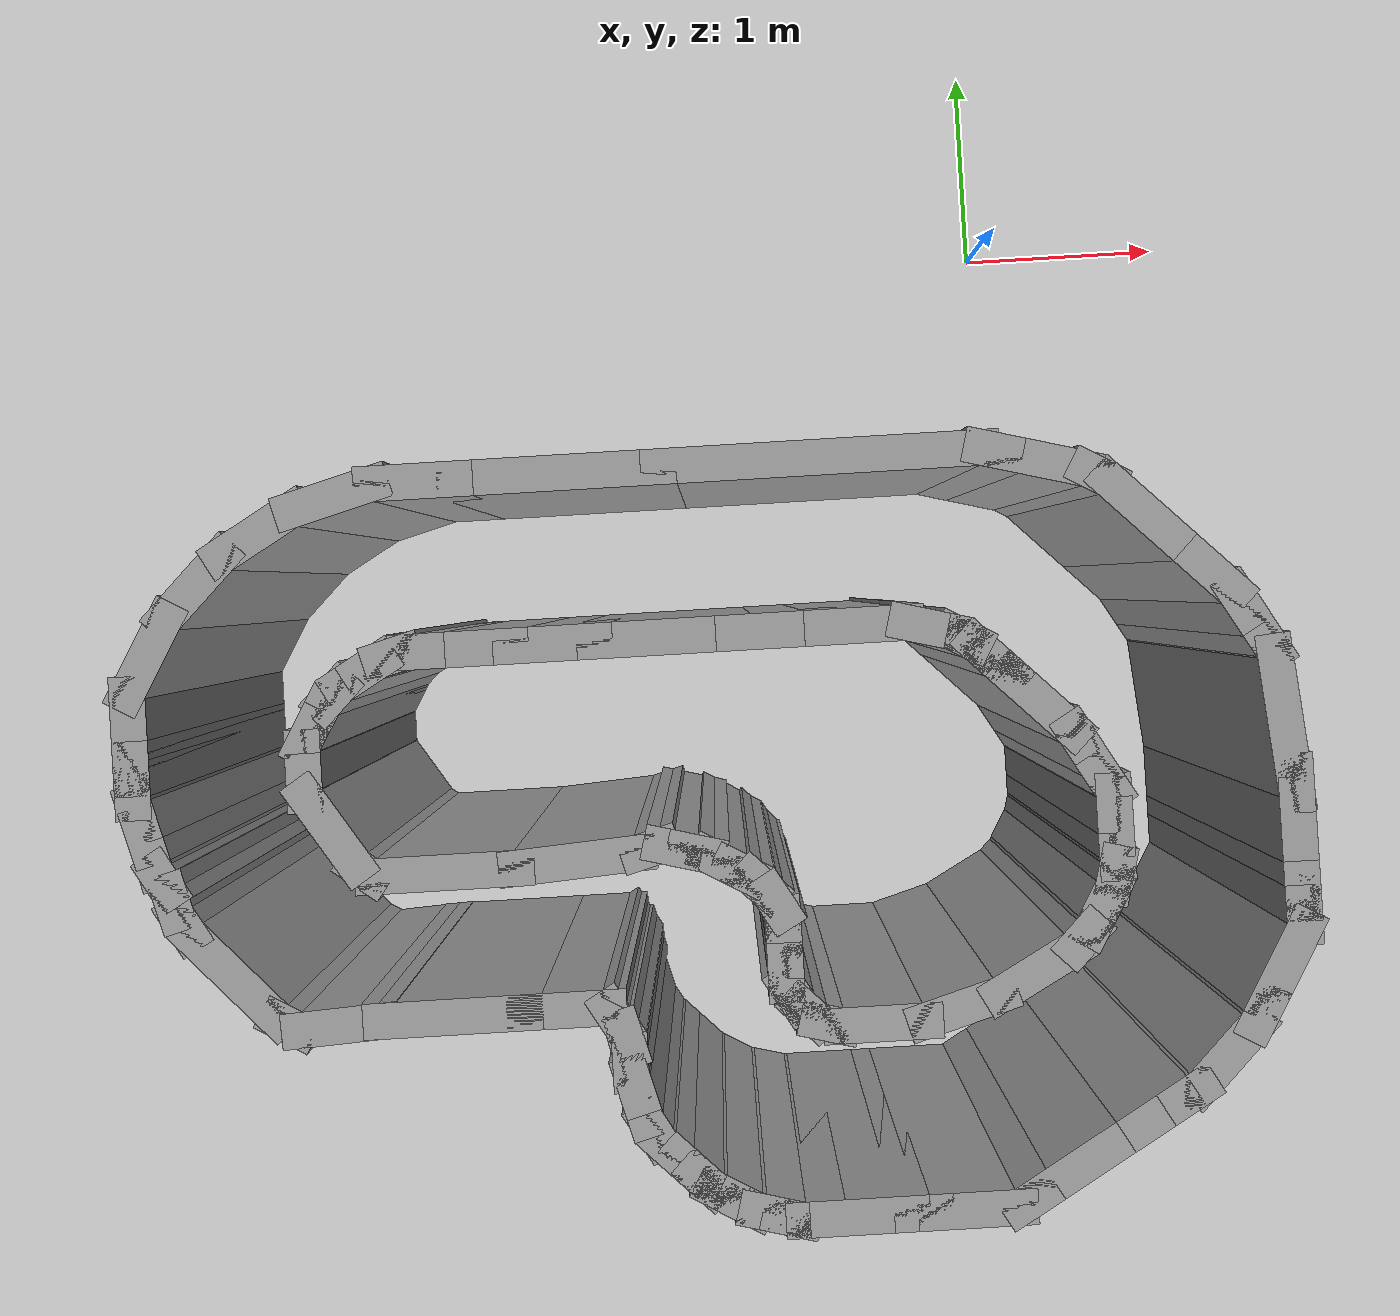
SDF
<?xml version='1.0'?>
<sdf version='1.7'>
  <world name="train_world">
      <!-- 基础环境 -->
      <include>
          <uri>model://sun</uri>
      </include>

      <include>
          <uri>model://ground_plane</uri>
      </include>

      <!-- 世界物理配置 - 让地面更坚硬 -->
      <physics type="ode">
          <real_time_update_rate>1000</real_time_update_rate>
          <real_time_factor>1</real_time_factor>
          <ode>
              <solver>
                  <type>quick</type>
                  <iters>50</iters>
                  <precon>1</precon>
                  <use_dynamic_moi_rescaling>1</use_dynamic_moi_rescaling>
              </solver>
              <constraints>
                  <cfm>0.00001</cfm>
                  <erp>0.8</erp>
                  <contact_max_correcting_vel>100</contact_max_correcting_vel>
                  <contact_surface_layer>0.001</contact_surface_layer>
              </constraints>
          </ode>
      </physics>
  <model name='test1'>
    <pose>-1.53943 -2.21966 0 0 -0 0</pose>
    <link name='Wall_0'>
      <collision name='Wall_0_Collision'>
        <geometry>
          <box>
            <size>0.75 0.15 2.5</size>
          </box>
        </geometry>
        <pose>0 0 1.25 0 -0 0</pose>
      </collision>
      <visual name='Wall_0_Visual'>
        <pose>0 0 1.25 0 -0 0</pose>
        <geometry>
          <box>
            <size>0.75 0.15 2.5</size>
          </box>
        </geometry>
        <material>
          <script>
            <uri>file://media/materials/scripts/gazebo.material</uri>
            <name>Gazebo/Grey</name>
          </script>
          <ambient>1 1 1 1</ambient>
        </material>
        <meta>
          <layer>0</layer>
        </meta>
      </visual>
      <pose>-1.14057 -1.19033 0 0 -0 0</pose>
    </link>
    <link name='Wall_10'>
      <collision name='Wall_10_Collision'>
        <geometry>
          <box>
            <size>0.25 0.15 2.5</size>
          </box>
        </geometry>
        <pose>0 0 1.25 0 -0 0</pose>
      </collision>
      <visual name='Wall_10_Visual'>
        <pose>0 0 1.25 0 -0 0</pose>
        <geometry>
          <box>
            <size>0.25 0.15 2.5</size>
          </box>
        </geometry>
        <material>
          <script>
            <uri>file://media/materials/scripts/gazebo.material</uri>
            <name>Gazebo/Grey</name>
          </script>
          <ambient>1 1 1 1</ambient>
        </material>
        <meta>
          <layer>0</layer>
        </meta>
      </visual>
      <pose>-1.48816 0.23169 0 0 -0 0.523599</pose>
    </link>
    <link name='Wall_100'>
      <collision name='Wall_100_Collision'>
        <geometry>
          <box>
            <size>0.25 0.15 2.5</size>
          </box>
        </geometry>
        <pose>0 0 1.25 0 -0 0</pose>
      </collision>
      <visual name='Wall_100_Visual'>
        <pose>0 0 1.25 0 -0 0</pose>
        <geometry>
          <box>
            <size>0.25 0.15 2.5</size>
          </box>
        </geometry>
        <material>
          <script>
            <uri>file://media/materials/scripts/gazebo.material</uri>
            <name>Gazebo/Grey</name>
          </script>
          <ambient>1 1 1 1</ambient>
        </material>
        <meta>
          <layer>0</layer>
        </meta>
      </visual>
      <pose>0.120704 -2.07839 0 0 -0 -0.261799</pose>
    </link>
    <link name='Wall_101'>
      <collision name='Wall_101_Collision'>
        <geometry>
          <box>
            <size>0.25 0.15 2.5</size>
          </box>
        </geometry>
        <pose>0 0 1.25 0 -0 0</pose>
      </collision>
      <visual name='Wall_101_Visual'>
        <pose>0 0 1.25 0 -0 0</pose>
        <geometry>
          <box>
            <size>0.25 0.15 2.5</size>
          </box>
        </geometry>
        <material>
          <script>
            <uri>file://media/materials/scripts/gazebo.material</uri>
            <name>Gazebo/Grey</name>
          </script>
          <ambient>1 1 1 1</ambient>
        </material>
        <meta>
          <layer>0</layer>
        </meta>
      </visual>
      <pose>0.217297 -2.10427 0 0 -0 -0.261799</pose>
    </link>
    <link name='Wall_102'>
      <collision name='Wall_102_Collision'>
        <geometry>
          <box>
            <size>0.25 0.15 2.5</size>
          </box>
        </geometry>
        <pose>0 0 1.25 0 -0 0</pose>
      </collision>
      <visual name='Wall_102_Visual'>
        <pose>0 0 1.25 0 -0 0</pose>
        <geometry>
          <box>
            <size>0.25 0.15 2.5</size>
          </box>
        </geometry>
        <material>
          <script>
            <uri>file://media/materials/scripts/gazebo.material</uri>
            <name>Gazebo/Grey</name>
          </script>
          <ambient>1 1 1 1</ambient>
        </material>
        <meta>
          <layer>0</layer>
        </meta>
      </visual>
      <pose>0.315593 -2.11721 0 0 -0 0</pose>
    </link>
    <link name='Wall_103'>
      <collision name='Wall_103_Collision'>
        <geometry>
          <box>
            <size>0.5 0.15 2.5</size>
          </box>
        </geometry>
        <pose>0 0 1.25 0 -0 0</pose>
      </collision>
      <visual name='Wall_103_Visual'>
        <pose>0 0 1.25 0 -0 0</pose>
        <geometry>
          <box>
            <size>0.5 0.15 2.5</size>
          </box>
        </geometry>
        <material>
          <script>
            <uri>file://media/materials/scripts/gazebo.material</uri>
            <name>Gazebo/Grey</name>
          </script>
          <ambient>1 1 1 1</ambient>
        </material>
        <meta>
          <layer>0</layer>
        </meta>
      </visual>
      <pose>0.540593 -2.11721 0 0 -0 0</pose>
    </link>
    <link name='Wall_104'>
      <collision name='Wall_104_Collision'>
        <geometry>
          <box>
            <size>0.25 0.15 2.5</size>
          </box>
        </geometry>
        <pose>0 0 1.25 0 -0 0</pose>
      </collision>
      <visual name='Wall_104_Visual'>
        <pose>0 0 1.25 0 -0 0</pose>
        <geometry>
          <box>
            <size>0.25 0.15 2.5</size>
          </box>
        </geometry>
        <material>
          <script>
            <uri>file://media/materials/scripts/gazebo.material</uri>
            <name>Gazebo/Grey</name>
          </script>
          <ambient>1 1 1 1</ambient>
        </material>
        <meta>
          <layer>0</layer>
        </meta>
      </visual>
      <pose>0.765593 -2.11721 0 0 -0 0</pose>
    </link>
    <link name='Wall_105'>
      <collision name='Wall_105_Collision'>
        <geometry>
          <box>
            <size>0.5 0.15 2.5</size>
          </box>
        </geometry>
        <pose>0 0 1.25 0 -0 0</pose>
      </collision>
      <visual name='Wall_105_Visual'>
        <pose>0 0 1.25 0 -0 0</pose>
        <geometry>
          <box>
            <size>0.5 0.15 2.5</size>
          </box>
        </geometry>
        <material>
          <script>
            <uri>file://media/materials/scripts/gazebo.material</uri>
            <name>Gazebo/Grey</name>
          </script>
          <ambient>1 1 1 1</ambient>
        </material>
        <meta>
          <layer>0</layer>
        </meta>
      </visual>
      <pose>0.990593 -2.11721 0 0 -0 0</pose>
    </link>
    <link name='Wall_11'>
      <collision name='Wall_11_Collision'>
        <geometry>
          <box>
            <size>0.25 0.15 2.5</size>
          </box>
        </geometry>
        <pose>0 0 1.25 0 -0 0</pose>
      </collision>
      <visual name='Wall_11_Visual'>
        <pose>0 0 1.25 0 -0 0</pose>
        <geometry>
          <box>
            <size>0.25 0.15 2.5</size>
          </box>
        </geometry>
        <material>
          <script>
            <uri>file://media/materials/scripts/gazebo.material</uri>
            <name>Gazebo/Grey</name>
          </script>
          <ambient>1 1 1 1</ambient>
        </material>
        <meta>
          <layer>0</layer>
        </meta>
      </visual>
      <pose>-1.40156 0.28169 0 0 -0 0.523599</pose>
    </link>
    <link name='Wall_110'>
      <collision name='Wall_110_Collision'>
        <geometry>
          <box>
            <size>0.25 0.15 2.5</size>
          </box>
        </geometry>
        <pose>0 0 1.25 0 -0 0</pose>
      </collision>
      <visual name='Wall_110_Visual'>
        <pose>0 0 1.25 0 -0 0</pose>
        <geometry>
          <box>
            <size>0.25 0.15 2.5</size>
          </box>
        </geometry>
        <material>
          <script>
            <uri>file://media/materials/scripts/gazebo.material</uri>
            <name>Gazebo/Grey</name>
          </script>
          <ambient>1 1 1 1</ambient>
        </material>
        <meta>
          <layer>0</layer>
        </meta>
      </visual>
      <pose>1.20889 -2.09221 0 0 -0 0.523599</pose>
    </link>
    <link name='Wall_111'>
      <collision name='Wall_111_Collision'>
        <geometry>
          <box>
            <size>0.5 0.15 2.5</size>
          </box>
        </geometry>
        <pose>0 0 1.25 0 -0 0</pose>
      </collision>
      <visual name='Wall_111_Visual'>
        <pose>0 0 1.25 0 -0 0</pose>
        <geometry>
          <box>
            <size>0.5 0.15 2.5</size>
          </box>
        </geometry>
        <material>
          <script>
            <uri>file://media/materials/scripts/gazebo.material</uri>
            <name>Gazebo/Grey</name>
          </script>
          <ambient>1 1 1 1</ambient>
        </material>
        <meta>
          <layer>0</layer>
        </meta>
      </visual>
      <pose>1.40375 -1.97971 0 0 -0 0.523599</pose>
    </link>
    <link name='Wall_112'>
      <collision name='Wall_112_Collision'>
        <geometry>
          <box>
            <size>0.5 0.15 2.5</size>
          </box>
        </geometry>
        <pose>0 0 1.25 0 -0 0</pose>
      </collision>
      <visual name='Wall_112_Visual'>
        <pose>0 0 1.25 0 -0 0</pose>
        <geometry>
          <box>
            <size>0.5 0.15 2.5</size>
          </box>
        </geometry>
        <material>
          <script>
            <uri>file://media/materials/scripts/gazebo.material</uri>
            <name>Gazebo/Grey</name>
          </script>
          <ambient>1 1 1 1</ambient>
        </material>
        <meta>
          <layer>0</layer>
        </meta>
      </visual>
      <pose>1.70686 -1.80471 0 0 -0 0.523599</pose>
    </link>
    <link name='Wall_113'>
      <collision name='Wall_113_Collision'>
        <geometry>
          <box>
            <size>0.25 0.15 2.5</size>
          </box>
        </geometry>
        <pose>0 0 1.25 0 -0 0</pose>
      </collision>
      <visual name='Wall_113_Visual'>
        <pose>0 0 1.25 0 -0 0</pose>
        <geometry>
          <box>
            <size>0.25 0.15 2.5</size>
          </box>
        </geometry>
        <material>
          <script>
            <uri>file://media/materials/scripts/gazebo.material</uri>
            <name>Gazebo/Grey</name>
          </script>
          <ambient>1 1 1 1</ambient>
        </material>
        <meta>
          <layer>0</layer>
        </meta>
      </visual>
      <pose>1.90172 -1.69221 0 0 -0 0.523599</pose>
    </link>
    <link name='Wall_114'>
      <collision name='Wall_114_Collision'>
        <geometry>
          <box>
            <size>0.5 0.15 2.5</size>
          </box>
        </geometry>
        <pose>0 0 1.25 0 -0 0</pose>
      </collision>
      <visual name='Wall_114_Visual'>
        <pose>0 0 1.25 0 -0 0</pose>
        <geometry>
          <box>
            <size>0.5 0.15 2.5</size>
          </box>
        </geometry>
        <material>
          <script>
            <uri>file://media/materials/scripts/gazebo.material</uri>
            <name>Gazebo/Grey</name>
          </script>
          <ambient>1 1 1 1</ambient>
        </material>
        <meta>
          <layer>0</layer>
        </meta>
      </visual>
      <pose>2.06876 -1.54347 0 0 -0 0.785398</pose>
    </link>
    <link name='Wall_115'>
      <collision name='Wall_115_Collision'>
        <geometry>
          <box>
            <size>0.25 0.15 2.5</size>
          </box>
        </geometry>
        <pose>0 0 1.25 0 -0 0</pose>
      </collision>
      <visual name='Wall_115_Visual'>
        <pose>0 0 1.25 0 -0 0</pose>
        <geometry>
          <box>
            <size>0.25 0.15 2.5</size>
          </box>
        </geometry>
        <material>
          <script>
            <uri>file://media/materials/scripts/gazebo.material</uri>
            <name>Gazebo/Grey</name>
          </script>
          <ambient>1 1 1 1</ambient>
        </material>
        <meta>
          <layer>0</layer>
        </meta>
      </visual>
      <pose>2.2175 -1.37643 0 0 -0 1.0472</pose>
    </link>
    <link name='Wall_116'>
      <collision name='Wall_116_Collision'>
        <geometry>
          <box>
            <size>0.5 0.15 2.5</size>
          </box>
        </geometry>
        <pose>0 0 1.25 0 -0 0</pose>
      </collision>
      <visual name='Wall_116_Visual'>
        <pose>0 0 1.25 0 -0 0</pose>
        <geometry>
          <box>
            <size>0.5 0.15 2.5</size>
          </box>
        </geometry>
        <material>
          <script>
            <uri>file://media/materials/scripts/gazebo.material</uri>
            <name>Gazebo/Grey</name>
          </script>
          <ambient>1 1 1 1</ambient>
        </material>
        <meta>
          <layer>0</layer>
        </meta>
      </visual>
      <pose>2.33 -1.18157 0 0 -0 1.0472</pose>
    </link>
    <link name='Wall_117'>
      <collision name='Wall_117_Collision'>
        <geometry>
          <box>
            <size>0.25 0.15 2.5</size>
          </box>
        </geometry>
        <pose>0 0 1.25 0 -0 0</pose>
      </collision>
      <visual name='Wall_117_Visual'>
        <pose>0 0 1.25 0 -0 0</pose>
        <geometry>
          <box>
            <size>0.25 0.15 2.5</size>
          </box>
        </geometry>
        <material>
          <script>
            <uri>file://media/materials/scripts/gazebo.material</uri>
            <name>Gazebo/Grey</name>
          </script>
          <ambient>1 1 1 1</ambient>
        </material>
        <meta>
          <layer>0</layer>
        </meta>
      </visual>
      <pose>2.4175 -0.980015 0 0 -0 1.5708</pose>
    </link>
    <link name='Wall_118'>
      <collision name='Wall_118_Collision'>
        <geometry>
          <box>
            <size>0.25 0.15 2.5</size>
          </box>
        </geometry>
        <pose>0 0 1.25 0 -0 0</pose>
      </collision>
      <visual name='Wall_118_Visual'>
        <pose>0 0 1.25 0 -0 0</pose>
        <geometry>
          <box>
            <size>0.25 0.15 2.5</size>
          </box>
        </geometry>
        <material>
          <script>
            <uri>file://media/materials/scripts/gazebo.material</uri>
            <name>Gazebo/Grey</name>
          </script>
          <ambient>1 1 1 1</ambient>
        </material>
        <meta>
          <layer>0</layer>
        </meta>
      </visual>
      <pose>2.4175 -0.880015 0 0 -0 1.5708</pose>
    </link>
    <link name='Wall_119'>
      <collision name='Wall_119_Collision'>
        <geometry>
          <box>
            <size>0.5 0.15 2.5</size>
          </box>
        </geometry>
        <pose>0 0 1.25 0 -0 0</pose>
      </collision>
      <visual name='Wall_119_Visual'>
        <pose>0 0 1.25 0 -0 0</pose>
        <geometry>
          <box>
            <size>0.5 0.15 2.5</size>
          </box>
        </geometry>
        <material>
          <script>
            <uri>file://media/materials/scripts/gazebo.material</uri>
            <name>Gazebo/Grey</name>
          </script>
          <ambient>1 1 1 1</ambient>
        </material>
        <meta>
          <layer>0</layer>
        </meta>
      </visual>
      <pose>2.4175 -0.655015 0 0 -0 1.5708</pose>
    </link>
    <link name='Wall_12'>
      <collision name='Wall_12_Collision'>
        <geometry>
          <box>
            <size>0.25 0.15 2.5</size>
          </box>
        </geometry>
        <pose>0 0 1.25 0 -0 0</pose>
      </collision>
      <visual name='Wall_12_Visual'>
        <pose>0 0 1.25 0 -0 0</pose>
        <geometry>
          <box>
            <size>0.25 0.15 2.5</size>
          </box>
        </geometry>
        <material>
          <script>
            <uri>file://media/materials/scripts/gazebo.material</uri>
            <name>Gazebo/Grey</name>
          </script>
          <ambient>1 1 1 1</ambient>
        </material>
        <meta>
          <layer>0</layer>
        </meta>
      </visual>
      <pose>-1.30997 0.319631 0 0 -0 0.261799</pose>
    </link>
    <link name='Wall_120'>
      <collision name='Wall_120_Collision'>
        <geometry>
          <box>
            <size>0.25 0.15 2.5</size>
          </box>
        </geometry>
        <pose>0 0 1.25 0 -0 0</pose>
      </collision>
      <visual name='Wall_120_Visual'>
        <pose>0 0 1.25 0 -0 0</pose>
        <geometry>
          <box>
            <size>0.25 0.15 2.5</size>
          </box>
        </geometry>
        <material>
          <script>
            <uri>file://media/materials/scripts/gazebo.material</uri>
            <name>Gazebo/Grey</name>
          </script>
          <ambient>1 1 1 1</ambient>
        </material>
        <meta>
          <layer>0</layer>
        </meta>
      </visual>
      <pose>2.4175 -0.430015 0 0 -0 1.5708</pose>
    </link>
    <link name='Wall_126'>
      <collision name='Wall_126_Collision'>
        <geometry>
          <box>
            <size>0.5 0.15 2.5</size>
          </box>
        </geometry>
        <pose>0 0 1.25 0 -0 0</pose>
      </collision>
      <visual name='Wall_126_Visual'>
        <pose>0 0 1.25 0 -0 0</pose>
        <geometry>
          <box>
            <size>0.5 0.15 2.5</size>
          </box>
        </geometry>
        <material>
          <script>
            <uri>file://media/materials/scripts/gazebo.material</uri>
            <name>Gazebo/Grey</name>
          </script>
          <ambient>1 1 1 1</ambient>
        </material>
        <meta>
          <layer>0</layer>
        </meta>
      </visual>
      <pose>-2.4175 0.050557 0 0 -0 1.5708</pose>
    </link>
    <link name='Wall_127'>
      <collision name='Wall_127_Collision'>
        <geometry>
          <box>
            <size>0.5 0.15 2.5</size>
          </box>
        </geometry>
        <pose>0 0 1.25 0 -0 0</pose>
      </collision>
      <visual name='Wall_127_Visual'>
        <pose>0 0 1.25 0 -0 0</pose>
        <geometry>
          <box>
            <size>0.5 0.15 2.5</size>
          </box>
        </geometry>
        <material>
          <script>
            <uri>file://media/materials/scripts/gazebo.material</uri>
            <name>Gazebo/Grey</name>
          </script>
          <ambient>1 1 1 1</ambient>
        </material>
        <meta>
          <layer>0</layer>
        </meta>
      </visual>
      <pose>-2.33 0.377112 0 0 -0 1.0472</pose>
    </link>
    <link name='Wall_128'>
      <collision name='Wall_128_Collision'>
        <geometry>
          <box>
            <size>0.5 0.15 2.5</size>
          </box>
        </geometry>
        <pose>0 0 1.25 0 -0 0</pose>
      </collision>
      <visual name='Wall_128_Visual'>
        <pose>0 0 1.25 0 -0 0</pose>
        <geometry>
          <box>
            <size>0.5 0.15 2.5</size>
          </box>
        </geometry>
        <material>
          <script>
            <uri>file://media/materials/scripts/gazebo.material</uri>
            <name>Gazebo/Grey</name>
          </script>
          <ambient>1 1 1 1</ambient>
        </material>
        <meta>
          <layer>0</layer>
        </meta>
      </visual>
      <pose>-2.11876 0.65241 0 0 -0 0.785398</pose>
    </link>
    <link name='Wall_129'>
      <collision name='Wall_129_Collision'>
        <geometry>
          <box>
            <size>0.5 0.15 2.5</size>
          </box>
        </geometry>
        <pose>0 0 1.25 0 -0 0</pose>
      </collision>
      <visual name='Wall_129_Visual'>
        <pose>0 0 1.25 0 -0 0</pose>
        <geometry>
          <box>
            <size>0.5 0.15 2.5</size>
          </box>
        </geometry>
        <material>
          <script>
            <uri>file://media/materials/scripts/gazebo.material</uri>
            <name>Gazebo/Grey</name>
          </script>
          <ambient>1 1 1 1</ambient>
        </material>
        <meta>
          <layer>0</layer>
        </meta>
      </visual>
      <pose>-1.84346 0.863653 0 0 -0 0.523599</pose>
    </link>
    <link name='Wall_13'>
      <collision name='Wall_13_Collision'>
        <geometry>
          <box>
            <size>0.25 0.15 2.5</size>
          </box>
        </geometry>
        <pose>0 0 1.25 0 -0 0</pose>
      </collision>
      <visual name='Wall_13_Visual'>
        <pose>0 0 1.25 0 -0 0</pose>
        <geometry>
          <box>
            <size>0.25 0.15 2.5</size>
          </box>
        </geometry>
        <material>
          <script>
            <uri>file://media/materials/scripts/gazebo.material</uri>
            <name>Gazebo/Grey</name>
          </script>
          <ambient>1 1 1 1</ambient>
        </material>
        <meta>
          <layer>0</layer>
        </meta>
      </visual>
      <pose>-1.21167 0.332572 0 0 -0 0</pose>
    </link>
    <link name='Wall_130'>
      <collision name='Wall_130_Collision'>
        <geometry>
          <box>
            <size>0.5 0.15 2.5</size>
          </box>
        </geometry>
        <pose>0 0 1.25 0 -0 0</pose>
      </collision>
      <visual name='Wall_130_Visual'>
        <pose>0 0 1.25 0 -0 0</pose>
        <geometry>
          <box>
            <size>0.5 0.15 2.5</size>
          </box>
        </geometry>
        <material>
          <script>
            <uri>file://media/materials/scripts/gazebo.material</uri>
            <name>Gazebo/Grey</name>
          </script>
          <ambient>1 1 1 1</ambient>
        </material>
        <meta>
          <layer>0</layer>
        </meta>
      </visual>
      <pose>-1.52287 0.996447 0 0 -0 0.261799</pose>
    </link>
    <link name='Wall_131'>
      <collision name='Wall_131_Collision'>
        <geometry>
          <box>
            <size>0.5 0.15 2.5</size>
          </box>
        </geometry>
        <pose>0 0 1.25 0 -0 0</pose>
      </collision>
      <visual name='Wall_131_Visual'>
        <pose>0 0 1.25 0 -0 0</pose>
        <geometry>
          <box>
            <size>0.5 0.15 2.5</size>
          </box>
        </geometry>
        <material>
          <script>
            <uri>file://media/materials/scripts/gazebo.material</uri>
            <name>Gazebo/Grey</name>
          </script>
          <ambient>1 1 1 1</ambient>
        </material>
        <meta>
          <layer>0</layer>
        </meta>
      </visual>
      <pose>-1.17883 1.04174 0 0 -0 0</pose>
    </link>
    <link name='Wall_132'>
      <collision name='Wall_132_Collision'>
        <geometry>
          <box>
            <size>1 0.15 2.5</size>
          </box>
        </geometry>
        <pose>0 0 1.25 0 -0 0</pose>
      </collision>
      <visual name='Wall_132_Visual'>
        <pose>0 0 1.25 0 -0 0</pose>
        <geometry>
          <box>
            <size>1 0.15 2.5</size>
          </box>
        </geometry>
        <material>
          <script>
            <uri>file://media/materials/scripts/gazebo.material</uri>
            <name>Gazebo/Grey</name>
          </script>
          <ambient>1 1 1 1</ambient>
        </material>
        <meta>
          <layer>0</layer>
        </meta>
      </visual>
      <pose>-0.578833 1.04174 0 0 -0 0</pose>
    </link>
    <link name='Wall_134'>
      <collision name='Wall_134_Collision'>
        <geometry>
          <box>
            <size>1.5 0.15 2.5</size>
          </box>
        </geometry>
        <pose>0 0 1.25 0 -0 0</pose>
      </collision>
      <visual name='Wall_134_Visual'>
        <pose>0 0 1.25 0 -0 0</pose>
        <geometry>
          <box>
            <size>1.5 0.15 2.5</size>
          </box>
        </geometry>
        <material>
          <script>
            <uri>file://media/materials/scripts/gazebo.material</uri>
            <name>Gazebo/Grey</name>
          </script>
          <ambient>1 1 1 1</ambient>
        </material>
        <meta>
          <layer>0</layer>
        </meta>
      </visual>
      <pose>0.521167 1.04174 0 0 -0 0</pose>
    </link>
    <link name='Wall_135'>
      <collision name='Wall_135_Collision'>
        <geometry>
          <box>
            <size>0.25 0.15 2.5</size>
          </box>
        </geometry>
        <pose>0 0 1.25 0 -0 0</pose>
      </collision>
      <visual name='Wall_135_Visual'>
        <pose>0 0 1.25 0 -0 0</pose>
        <geometry>
          <box>
            <size>0.25 0.15 2.5</size>
          </box>
        </geometry>
        <material>
          <script>
            <uri>file://media/materials/scripts/gazebo.material</uri>
            <name>Gazebo/Grey</name>
          </script>
          <ambient>1 1 1 1</ambient>
        </material>
        <meta>
          <layer>0</layer>
        </meta>
      </visual>
      <pose>1.24446 1.0288 0 0 -0 -0.261799</pose>
    </link>
    <link name='Wall_136'>
      <collision name='Wall_136_Collision'>
        <geometry>
          <box>
            <size>0.5 0.15 2.5</size>
          </box>
        </geometry>
        <pose>0 0 1.25 0 -0 0</pose>
      </collision>
      <visual name='Wall_136_Visual'>
        <pose>0 0 1.25 0 -0 0</pose>
        <geometry>
          <box>
            <size>0.5 0.15 2.5</size>
          </box>
        </geometry>
        <material>
          <script>
            <uri>file://media/materials/scripts/gazebo.material</uri>
            <name>Gazebo/Grey</name>
          </script>
          <ambient>1 1 1 1</ambient>
        </material>
        <meta>
          <layer>0</layer>
        </meta>
      </visual>
      <pose>1.4618 0.970565 0 0 -0 -0.261799</pose>
    </link>
    <link name='Wall_137'>
      <collision name='Wall_137_Collision'>
        <geometry>
          <box>
            <size>0.25 0.15 2.5</size>
          </box>
        </geometry>
        <pose>0 0 1.25 0 -0 0</pose>
      </collision>
      <visual name='Wall_137_Visual'>
        <pose>0 0 1.25 0 -0 0</pose>
        <geometry>
          <box>
            <size>0.25 0.15 2.5</size>
          </box>
        </geometry>
        <material>
          <script>
            <uri>file://media/materials/scripts/gazebo.material</uri>
            <name>Gazebo/Grey</name>
          </script>
          <ambient>1 1 1 1</ambient>
        </material>
        <meta>
          <layer>0</layer>
        </meta>
      </visual>
      <pose>1.67413 0.900272 0 0 -0 -0.523599</pose>
    </link>
    <link name='Wall_138'>
      <collision name='Wall_138_Collision'>
        <geometry>
          <box>
            <size>0.5 0.15 2.5</size>
          </box>
        </geometry>
        <pose>0 0 1.25 0 -0 0</pose>
      </collision>
      <visual name='Wall_138_Visual'>
        <pose>0 0 1.25 0 -0 0</pose>
        <geometry>
          <box>
            <size>0.5 0.15 2.5</size>
          </box>
        </geometry>
        <material>
          <script>
            <uri>file://media/materials/scripts/gazebo.material</uri>
            <name>Gazebo/Grey</name>
          </script>
          <ambient>1 1 1 1</ambient>
        </material>
        <meta>
          <layer>0</layer>
        </meta>
      </visual>
      <pose>1.84118 0.751528 0 0 -0 -0.785398</pose>
    </link>
    <link name='Wall_139'>
      <collision name='Wall_139_Collision'>
        <geometry>
          <box>
            <size>0.5 0.15 2.5</size>
          </box>
        </geometry>
        <pose>0 0 1.25 0 -0 0</pose>
      </collision>
      <visual name='Wall_139_Visual'>
        <pose>0 0 1.25 0 -0 0</pose>
        <geometry>
          <box>
            <size>0.5 0.15 2.5</size>
          </box>
        </geometry>
        <material>
          <script>
            <uri>file://media/materials/scripts/gazebo.material</uri>
            <name>Gazebo/Grey</name>
          </script>
          <ambient>1 1 1 1</ambient>
        </material>
        <meta>
          <layer>0</layer>
        </meta>
      </visual>
      <pose>2.08867 0.50404 0 0 -0 -0.785398</pose>
    </link>
    <link name='Wall_14'>
      <collision name='Wall_14_Collision'>
        <geometry>
          <box>
            <size>0.5 0.15 2.5</size>
          </box>
        </geometry>
        <pose>0 0 1.25 0 -0 0</pose>
      </collision>
      <visual name='Wall_14_Visual'>
        <pose>0 0 1.25 0 -0 0</pose>
        <geometry>
          <box>
            <size>0.5 0.15 2.5</size>
          </box>
        </geometry>
        <material>
          <script>
            <uri>file://media/materials/scripts/gazebo.material</uri>
            <name>Gazebo/Grey</name>
          </script>
          <ambient>1 1 1 1</ambient>
        </material>
        <meta>
          <layer>0</layer>
        </meta>
      </visual>
      <pose>-0.986669 0.332572 0 0 -0 0</pose>
    </link>
    <link name='Wall_140'>
      <collision name='Wall_140_Collision'>
        <geometry>
          <box>
            <size>0.25 0.15 2.5</size>
          </box>
        </geometry>
        <pose>0 0 1.25 0 -0 0</pose>
      </collision>
      <visual name='Wall_140_Visual'>
        <pose>0 0 1.25 0 -0 0</pose>
        <geometry>
          <box>
            <size>0.25 0.15 2.5</size>
          </box>
        </geometry>
        <material>
          <script>
            <uri>file://media/materials/scripts/gazebo.material</uri>
            <name>Gazebo/Grey</name>
          </script>
          <ambient>1 1 1 1</ambient>
        </material>
        <meta>
          <layer>0</layer>
        </meta>
      </visual>
      <pose>2.23741 0.336995 0 0 -0 -1.0472</pose>
    </link>
    <link name='Wall_141'>
      <collision name='Wall_141_Collision'>
        <geometry>
          <box>
            <size>0.25 0.15 2.5</size>
          </box>
        </geometry>
        <pose>0 0 1.25 0 -0 0</pose>
      </collision>
      <visual name='Wall_141_Visual'>
        <pose>0 0 1.25 0 -0 0</pose>
        <geometry>
          <box>
            <size>0.25 0.15 2.5</size>
          </box>
        </geometry>
        <material>
          <script>
            <uri>file://media/materials/scripts/gazebo.material</uri>
            <name>Gazebo/Grey</name>
          </script>
          <ambient>1 1 1 1</ambient>
        </material>
        <meta>
          <layer>0</layer>
        </meta>
      </visual>
      <pose>2.28741 0.250393 0 0 -0 -1.0472</pose>
    </link>
    <link name='Wall_142'>
      <collision name='Wall_142_Collision'>
        <geometry>
          <box>
            <size>0.25 0.15 2.5</size>
          </box>
        </geometry>
        <pose>0 0 1.25 0 -0 0</pose>
      </collision>
      <visual name='Wall_142_Visual'>
        <pose>0 0 1.25 0 -0 0</pose>
        <geometry>
          <box>
            <size>0.25 0.15 2.5</size>
          </box>
        </geometry>
        <material>
          <script>
            <uri>file://media/materials/scripts/gazebo.material</uri>
            <name>Gazebo/Grey</name>
          </script>
          <ambient>1 1 1 1</ambient>
        </material>
        <meta>
          <layer>0</layer>
        </meta>
      </visual>
      <pose>2.33741 0.16379 0 0 -0 -1.0472</pose>
    </link>
    <link name='Wall_143'>
      <collision name='Wall_143_Collision'>
        <geometry>
          <box>
            <size>0.753026 0.15 2.5</size>
          </box>
        </geometry>
        <pose>0 0 1.25 0 -0 0</pose>
      </collision>
      <visual name='Wall_143_Visual'>
        <pose>0 0 1.25 0 -0 0</pose>
        <geometry>
          <box>
            <size>0.753026 0.15 2.5</size>
          </box>
        </geometry>
        <material>
          <script>
            <uri>file://media/materials/scripts/gazebo.material</uri>
            <name>Gazebo/Grey</name>
          </script>
          <ambient>1 1 1 1</ambient>
        </material>
        <meta>
          <layer>0</layer>
        </meta>
      </visual>
      <pose>2.38996 -0.179763 0 0 -0 -1.47931</pose>
    </link>
    <link name='Wall_15'>
      <collision name='Wall_15_Collision'>
        <geometry>
          <box>
            <size>0.5 0.15 2.5</size>
          </box>
        </geometry>
        <pose>0 0 1.25 0 -0 0</pose>
      </collision>
      <visual name='Wall_15_Visual'>
        <pose>0 0 1.25 0 -0 0</pose>
        <geometry>
          <box>
            <size>0.5 0.15 2.5</size>
          </box>
        </geometry>
        <material>
          <script>
            <uri>file://media/materials/scripts/gazebo.material</uri>
            <name>Gazebo/Grey</name>
          </script>
          <ambient>1 1 1 1</ambient>
        </material>
        <meta>
          <layer>0</layer>
        </meta>
      </visual>
      <pose>-0.636669 0.332572 0 0 -0 0</pose>
    </link>
    <link name='Wall_16'>
      <collision name='Wall_16_Collision'>
        <geometry>
          <box>
            <size>0.73 0.15 2.5</size>
          </box>
        </geometry>
        <pose>0 0 1.25 0 -0 0</pose>
      </collision>
      <visual name='Wall_16_Visual'>
        <pose>0 0 1.25 0 -0 0</pose>
        <geometry>
          <box>
            <size>0.73 0.15 2.5</size>
          </box>
        </geometry>
        <material>
          <script>
            <uri>file://media/materials/scripts/gazebo.material</uri>
            <name>Gazebo/Grey</name>
          </script>
          <ambient>1 1 1 1</ambient>
        </material>
        <meta>
          <layer>0</layer>
        </meta>
      </visual>
      <pose>-0.171669 0.332572 0 0 -0 0</pose>
    </link>
    <link name='Wall_17'>
      <collision name='Wall_17_Collision'>
        <geometry>
          <box>
            <size>0.52 0.15 2.5</size>
          </box>
        </geometry>
        <pose>0 0 1.25 0 -0 0</pose>
      </collision>
      <visual name='Wall_17_Visual'>
        <pose>0 0 1.25 0 -0 0</pose>
        <geometry>
          <box>
            <size>0.52 0.15 2.5</size>
          </box>
        </geometry>
        <material>
          <script>
            <uri>file://media/materials/scripts/gazebo.material</uri>
            <name>Gazebo/Grey</name>
          </script>
          <ambient>1 1 1 1</ambient>
        </material>
        <meta>
          <layer>0</layer>
        </meta>
      </visual>
      <pose>0.303331 0.332572 0 0 -0 0</pose>
    </link>
    <link name='Wall_18'>
      <collision name='Wall_18_Collision'>
        <geometry>
          <box>
            <size>0.5 0.15 2.5</size>
          </box>
        </geometry>
        <pose>0 0 1.25 0 -0 0</pose>
      </collision>
      <visual name='Wall_18_Visual'>
        <pose>0 0 1.25 0 -0 0</pose>
        <geometry>
          <box>
            <size>0.5 0.15 2.5</size>
          </box>
        </geometry>
        <material>
          <script>
            <uri>file://media/materials/scripts/gazebo.material</uri>
            <name>Gazebo/Grey</name>
          </script>
          <ambient>1 1 1 1</ambient>
        </material>
        <meta>
          <layer>0</layer>
        </meta>
      </visual>
      <pose>0.663331 0.332572 0 0 -0 0</pose>
    </link>
    <link name='Wall_19'>
      <collision name='Wall_19_Collision'>
        <geometry>
          <box>
            <size>0.25 0.15 2.5</size>
          </box>
        </geometry>
        <pose>0 0 1.25 0 -0 0</pose>
      </collision>
      <visual name='Wall_19_Visual'>
        <pose>0 0 1.25 0 -0 0</pose>
        <geometry>
          <box>
            <size>0.25 0.15 2.5</size>
          </box>
        </geometry>
        <material>
          <script>
            <uri>file://media/materials/scripts/gazebo.material</uri>
            <name>Gazebo/Grey</name>
          </script>
          <ambient>1 1 1 1</ambient>
        </material>
        <meta>
          <layer>0</layer>
        </meta>
      </visual>
      <pose>0.886627 0.319631 0 0 -0 -0.261799</pose>
    </link>
    <link name='Wall_2'>
      <collision name='Wall_2_Collision'>
        <geometry>
          <box>
            <size>0.75 0.15 2.5</size>
          </box>
        </geometry>
        <pose>0 0 1.25 0 -0 0</pose>
      </collision>
      <visual name='Wall_2_Visual'>
        <pose>0 0 1.25 0 -0 0</pose>
        <geometry>
          <box>
            <size>0.75 0.15 2.5</size>
          </box>
        </geometry>
        <material>
          <script>
            <uri>file://media/materials/scripts/gazebo.material</uri>
            <name>Gazebo/Grey</name>
          </script>
          <ambient>1 1 1 1</ambient>
        </material>
        <meta>
          <layer>0</layer>
        </meta>
      </visual>
      <pose>-1.14057 -0.590335 0 0 -0 3.14159</pose>
    </link>
    <link name='Wall_20'>
      <collision name='Wall_20_Collision'>
        <geometry>
          <box>
            <size>0.25 0.15 2.5</size>
          </box>
        </geometry>
        <pose>0 0 1.25 0 -0 0</pose>
      </collision>
      <visual name='Wall_20_Visual'>
        <pose>0 0 1.25 0 -0 0</pose>
        <geometry>
          <box>
            <size>0.25 0.15 2.5</size>
          </box>
        </geometry>
        <material>
          <script>
            <uri>file://media/materials/scripts/gazebo.material</uri>
            <name>Gazebo/Grey</name>
          </script>
          <ambient>1 1 1 1</ambient>
        </material>
        <meta>
          <layer>0</layer>
        </meta>
      </visual>
      <pose>0.98322 0.293749 0 0 -0 -0.261799</pose>
    </link>
    <link name='Wall_21'>
      <collision name='Wall_21_Collision'>
        <geometry>
          <box>
            <size>0.25 0.15 2.5</size>
          </box>
        </geometry>
        <pose>0 0 1.25 0 -0 0</pose>
      </collision>
      <visual name='Wall_21_Visual'>
        <pose>0 0 1.25 0 -0 0</pose>
        <geometry>
          <box>
            <size>0.25 0.15 2.5</size>
          </box>
        </geometry>
        <material>
          <script>
            <uri>file://media/materials/scripts/gazebo.material</uri>
            <name>Gazebo/Grey</name>
          </script>
          <ambient>1 1 1 1</ambient>
        </material>
        <meta>
          <layer>0</layer>
        </meta>
      </visual>
      <pose>1.07482 0.255808 0 0 -0 -0.523599</pose>
    </link>
    <link name='Wall_22'>
      <collision name='Wall_22_Collision'>
        <geometry>
          <box>
            <size>0.25 0.15 2.5</size>
          </box>
        </geometry>
        <pose>0 0 1.25 0 -0 0</pose>
      </collision>
      <visual name='Wall_22_Visual'>
        <pose>0 0 1.25 0 -0 0</pose>
        <geometry>
          <box>
            <size>0.25 0.15 2.5</size>
          </box>
        </geometry>
        <material>
          <script>
            <uri>file://media/materials/scripts/gazebo.material</uri>
            <name>Gazebo/Grey</name>
          </script>
          <ambient>1 1 1 1</ambient>
        </material>
        <meta>
          <layer>0</layer>
        </meta>
      </visual>
      <pose>1.15347 0.195453 0 0 -0 -0.785398</pose>
    </link>
    <link name='Wall_23'>
      <collision name='Wall_23_Collision'>
        <geometry>
          <box>
            <size>0.25 0.15 2.5</size>
          </box>
        </geometry>
        <pose>0 0 1.25 0 -0 0</pose>
      </collision>
      <visual name='Wall_23_Visual'>
        <pose>0 0 1.25 0 -0 0</pose>
        <geometry>
          <box>
            <size>0.25 0.15 2.5</size>
          </box>
        </geometry>
        <material>
          <script>
            <uri>file://media/materials/scripts/gazebo.material</uri>
            <name>Gazebo/Grey</name>
          </script>
          <ambient>1 1 1 1</ambient>
        </material>
        <meta>
          <layer>0</layer>
        </meta>
      </visual>
      <pose>1.22419 0.124742 0 0 -0 -0.785398</pose>
    </link>
    <link name='Wall_24'>
      <collision name='Wall_24_Collision'>
        <geometry>
          <box>
            <size>0.5 0.15 2.5</size>
          </box>
        </geometry>
        <pose>0 0 1.25 0 -0 0</pose>
      </collision>
      <visual name='Wall_24_Visual'>
        <pose>0 0 1.25 0 -0 0</pose>
        <geometry>
          <box>
            <size>0.5 0.15 2.5</size>
          </box>
        </geometry>
        <material>
          <script>
            <uri>file://media/materials/scripts/gazebo.material</uri>
            <name>Gazebo/Grey</name>
          </script>
          <ambient>1 1 1 1</ambient>
        </material>
        <meta>
          <layer>0</layer>
        </meta>
      </visual>
      <pose>1.38328 -0.034357 0 0 -0 -0.785398</pose>
    </link>
    <link name='Wall_25'>
      <collision name='Wall_25_Collision'>
        <geometry>
          <box>
            <size>0.25 0.15 2.5</size>
          </box>
        </geometry>
        <pose>0 0 1.25 0 -0 0</pose>
      </collision>
      <visual name='Wall_25_Visual'>
        <pose>0 0 1.25 0 -0 0</pose>
        <geometry>
          <box>
            <size>0.25 0.15 2.5</size>
          </box>
        </geometry>
        <material>
          <script>
            <uri>file://media/materials/scripts/gazebo.material</uri>
            <name>Gazebo/Grey</name>
          </script>
          <ambient>1 1 1 1</ambient>
        </material>
        <meta>
          <layer>0</layer>
        </meta>
      </visual>
      <pose>1.53203 -0.201402 0 0 -0 -1.0472</pose>
    </link>
    <link name='Wall_26'>
      <collision name='Wall_26_Collision'>
        <geometry>
          <box>
            <size>0.25 0.15 2.5</size>
          </box>
        </geometry>
        <pose>0 0 1.25 0 -0 0</pose>
      </collision>
      <visual name='Wall_26_Visual'>
        <pose>0 0 1.25 0 -0 0</pose>
        <geometry>
          <box>
            <size>0.25 0.15 2.5</size>
          </box>
        </geometry>
        <material>
          <script>
            <uri>file://media/materials/scripts/gazebo.material</uri>
            <name>Gazebo/Grey</name>
          </script>
          <ambient>1 1 1 1</ambient>
        </material>
        <meta>
          <layer>0</layer>
        </meta>
      </visual>
      <pose>1.58203 -0.288004 0 0 -0 -1.0472</pose>
    </link>
    <link name='Wall_27'>
      <collision name='Wall_27_Collision'>
        <geometry>
          <box>
            <size>0.25 0.15 2.5</size>
          </box>
        </geometry>
        <pose>0 0 1.25 0 -0 0</pose>
      </collision>
      <visual name='Wall_27_Visual'>
        <pose>0 0 1.25 0 -0 0</pose>
        <geometry>
          <box>
            <size>0.25 0.15 2.5</size>
          </box>
        </geometry>
        <material>
          <script>
            <uri>file://media/materials/scripts/gazebo.material</uri>
            <name>Gazebo/Grey</name>
          </script>
          <ambient>1 1 1 1</ambient>
        </material>
        <meta>
          <layer>0</layer>
        </meta>
      </visual>
      <pose>1.63203 -0.374607 0 0 -0 -1.0472</pose>
    </link>
    <link name='Wall_28'>
      <collision name='Wall_28_Collision'>
        <geometry>
          <box>
            <size>0.25 0.15 2.5</size>
          </box>
        </geometry>
        <pose>0 0 1.25 0 -0 0</pose>
      </collision>
      <visual name='Wall_28_Visual'>
        <pose>0 0 1.25 0 -0 0</pose>
        <geometry>
          <box>
            <size>0.25 0.15 2.5</size>
          </box>
        </geometry>
        <material>
          <script>
            <uri>file://media/materials/scripts/gazebo.material</uri>
            <name>Gazebo/Grey</name>
          </script>
          <ambient>1 1 1 1</ambient>
        </material>
        <meta>
          <layer>0</layer>
        </meta>
      </visual>
      <pose>1.65703 -0.467908 0 0 -0 -1.5708</pose>
    </link>
    <link name='Wall_29'>
      <collision name='Wall_29_Collision'>
        <geometry>
          <box>
            <size>0.25 0.15 2.5</size>
          </box>
        </geometry>
        <pose>0 0 1.25 0 -0 0</pose>
      </collision>
      <visual name='Wall_29_Visual'>
        <pose>0 0 1.25 0 -0 0</pose>
        <geometry>
          <box>
            <size>0.25 0.15 2.5</size>
          </box>
        </geometry>
        <material>
          <script>
            <uri>file://media/materials/scripts/gazebo.material</uri>
            <name>Gazebo/Grey</name>
          </script>
          <ambient>1 1 1 1</ambient>
        </material>
        <meta>
          <layer>0</layer>
        </meta>
      </visual>
      <pose>1.65703 -0.567908 0 0 -0 -1.5708</pose>
    </link>
    <link name='Wall_3'>
      <collision name='Wall_3_Collision'>
        <geometry>
          <box>
            <size>0.233282 0.15 2.5</size>
          </box>
        </geometry>
        <pose>0 0 1.25 0 -0 0</pose>
      </collision>
      <visual name='Wall_3_Visual'>
        <pose>0 0 1.25 0 -0 0</pose>
        <geometry>
          <box>
            <size>0.233282 0.15 2.5</size>
          </box>
        </geometry>
        <material>
          <script>
            <uri>file://media/materials/scripts/gazebo.material</uri>
            <name>Gazebo/Grey</name>
          </script>
          <ambient>1 1 1 1</ambient>
        </material>
        <meta>
          <layer>0</layer>
        </meta>
      </visual>
      <pose>-1.47388 -0.565335 0 0 -0 2.49763</pose>
    </link>
    <link name='Wall_30'>
      <collision name='Wall_30_Collision'>
        <geometry>
          <box>
            <size>0.25 0.15 2.5</size>
          </box>
        </geometry>
        <pose>0 0 1.25 0 -0 0</pose>
      </collision>
      <visual name='Wall_30_Visual'>
        <pose>0 0 1.25 0 -0 0</pose>
        <geometry>
          <box>
            <size>0.25 0.15 2.5</size>
          </box>
        </geometry>
        <material>
          <script>
            <uri>file://media/materials/scripts/gazebo.material</uri>
            <name>Gazebo/Grey</name>
          </script>
          <ambient>1 1 1 1</ambient>
        </material>
        <meta>
          <layer>0</layer>
        </meta>
      </visual>
      <pose>1.65703 -0.667908 0 0 -0 -1.5708</pose>
    </link>
    <link name='Wall_31'>
      <collision name='Wall_31_Collision'>
        <geometry>
          <box>
            <size>0.25 0.15 2.5</size>
          </box>
        </geometry>
        <pose>0 0 1.25 0 -0 0</pose>
      </collision>
      <visual name='Wall_31_Visual'>
        <pose>0 0 1.25 0 -0 0</pose>
        <geometry>
          <box>
            <size>0.25 0.15 2.5</size>
          </box>
        </geometry>
        <material>
          <script>
            <uri>file://media/materials/scripts/gazebo.material</uri>
            <name>Gazebo/Grey</name>
          </script>
          <ambient>1 1 1 1</ambient>
        </material>
        <meta>
          <layer>0</layer>
        </meta>
      </visual>
      <pose>1.64409 -0.766205 0 0 -0 -1.8326</pose>
    </link>
    <link name='Wall_32'>
      <collision name='Wall_32_Collision'>
        <geometry>
          <box>
            <size>0.25 0.15 2.5</size>
          </box>
        </geometry>
        <pose>0 0 1.25 0 -0 0</pose>
      </collision>
      <visual name='Wall_32_Visual'>
        <pose>0 0 1.25 0 -0 0</pose>
        <geometry>
          <box>
            <size>0.25 0.15 2.5</size>
          </box>
        </geometry>
        <material>
          <script>
            <uri>file://media/materials/scripts/gazebo.material</uri>
            <name>Gazebo/Grey</name>
          </script>
          <ambient>1 1 1 1</ambient>
        </material>
        <meta>
          <layer>0</layer>
        </meta>
      </visual>
      <pose>1.60615 -0.857802 0 0 -0 -2.0944</pose>
    </link>
    <link name='Wall_33'>
      <collision name='Wall_33_Collision'>
        <geometry>
          <box>
            <size>0.25 0.15 2.5</size>
          </box>
        </geometry>
        <pose>0 0 1.25 0 -0 0</pose>
      </collision>
      <visual name='Wall_33_Visual'>
        <pose>0 0 1.25 0 -0 0</pose>
        <geometry>
          <box>
            <size>0.25 0.15 2.5</size>
          </box>
        </geometry>
        <material>
          <script>
            <uri>file://media/materials/scripts/gazebo.material</uri>
            <name>Gazebo/Grey</name>
          </script>
          <ambient>1 1 1 1</ambient>
        </material>
        <meta>
          <layer>0</layer>
        </meta>
      </visual>
      <pose>1.55615 -0.944405 0 0 -0 -2.0944</pose>
    </link>
    <link name='Wall_34'>
      <collision name='Wall_34_Collision'>
        <geometry>
          <box>
            <size>0.25 0.15 2.5</size>
          </box>
        </geometry>
        <pose>0 0 1.25 0 -0 0</pose>
      </collision>
      <visual name='Wall_34_Visual'>
        <pose>0 0 1.25 0 -0 0</pose>
        <geometry>
          <box>
            <size>0.25 0.15 2.5</size>
          </box>
        </geometry>
        <material>
          <script>
            <uri>file://media/materials/scripts/gazebo.material</uri>
            <name>Gazebo/Grey</name>
          </script>
          <ambient>1 1 1 1</ambient>
        </material>
        <meta>
          <layer>0</layer>
        </meta>
      </visual>
      <pose>1.49579 -1.02306 0 0 -0 -2.35619</pose>
    </link>
    <link name='Wall_35'>
      <collision name='Wall_35_Collision'>
        <geometry>
          <box>
            <size>0.517457 0.15 2.5</size>
          </box>
        </geometry>
        <pose>0 0 1.25 0 -0 0</pose>
      </collision>
      <visual name='Wall_35_Visual'>
        <pose>0 0 1.25 0 -0 0</pose>
        <geometry>
          <box>
            <size>0.517457 0.15 2.5</size>
          </box>
        </geometry>
        <material>
          <script>
            <uri>file://media/materials/scripts/gazebo.material</uri>
            <name>Gazebo/Grey</name>
          </script>
          <ambient>1 1 1 1</ambient>
        </material>
        <meta>
          <layer>0</layer>
        </meta>
      </visual>
      <pose>1.29888 -1.14592 0 0 -0 -2.64521</pose>
    </link>
    <link name='Wall_36'>
      <collision name='Wall_36_Collision'>
        <geometry>
          <box>
            <size>0.480722 0.15 2.5</size>
          </box>
        </geometry>
        <pose>0 0 1.25 0 -0 0</pose>
      </collision>
      <visual name='Wall_36_Visual'>
        <pose>0 0 1.25 0 -0 0</pose>
        <geometry>
          <box>
            <size>0.480722 0.15 2.5</size>
          </box>
        </geometry>
        <material>
          <script>
            <uri>file://media/materials/scripts/gazebo.material</uri>
            <name>Gazebo/Grey</name>
          </script>
          <ambient>1 1 1 1</ambient>
        </material>
        <meta>
          <layer>0</layer>
        </meta>
      </visual>
      <pose>0.978289 -1.27871 0 0 -0 -2.86414</pose>
    </link>
    <link name='Wall_37'>
      <collision name='Wall_37_Collision'>
        <geometry>
          <box>
            <size>0.5 0.15 2.5</size>
          </box>
        </geometry>
        <pose>0 0 1.25 0 -0 0</pose>
      </collision>
      <visual name='Wall_37_Visual'>
        <pose>0 0 1.25 0 -0 0</pose>
        <geometry>
          <box>
            <size>0.5 0.15 2.5</size>
          </box>
        </geometry>
        <material>
          <script>
            <uri>file://media/materials/scripts/gazebo.material</uri>
            <name>Gazebo/Grey</name>
          </script>
          <ambient>1 1 1 1</ambient>
        </material>
        <meta>
          <layer>0</layer>
        </meta>
      </visual>
      <pose>0.644252 -1.324 0 0 -0 3.14159</pose>
    </link>
    <link name='Wall_38'>
      <collision name='Wall_38_Collision'>
        <geometry>
          <box>
            <size>0.25 0.15 2.5</size>
          </box>
        </geometry>
        <pose>0 0 1.25 0 -0 0</pose>
      </collision>
      <visual name='Wall_38_Visual'>
        <pose>0 0 1.25 0 -0 0</pose>
        <geometry>
          <box>
            <size>0.25 0.15 2.5</size>
          </box>
        </geometry>
        <material>
          <script>
            <uri>file://media/materials/scripts/gazebo.material</uri>
            <name>Gazebo/Grey</name>
          </script>
          <ambient>1 1 1 1</ambient>
        </material>
        <meta>
          <layer>0</layer>
        </meta>
      </visual>
      <pose>0.420956 -1.31106 0 0 -0 2.87979</pose>
    </link>
    <link name='Wall_39'>
      <collision name='Wall_39_Collision'>
        <geometry>
          <box>
            <size>0.25 0.15 2.5</size>
          </box>
        </geometry>
        <pose>0 0 1.25 0 -0 0</pose>
      </collision>
      <visual name='Wall_39_Visual'>
        <pose>0 0 1.25 0 -0 0</pose>
        <geometry>
          <box>
            <size>0.25 0.15 2.5</size>
          </box>
        </geometry>
        <material>
          <script>
            <uri>file://media/materials/scripts/gazebo.material</uri>
            <name>Gazebo/Grey</name>
          </script>
          <ambient>1 1 1 1</ambient>
        </material>
        <meta>
          <layer>0</layer>
        </meta>
      </visual>
      <pose>0.337304 -1.26277 0 0 -0 2.35619</pose>
    </link>
    <link name='Wall_4'>
      <collision name='Wall_4_Collision'>
        <geometry>
          <box>
            <size>0.510416 0.15 2.5</size>
          </box>
        </geometry>
        <pose>0 0 1.25 0 -0 0</pose>
      </collision>
      <visual name='Wall_4_Visual'>
        <pose>0 0 1.25 0 -0 0</pose>
        <geometry>
          <box>
            <size>0.510416 0.15 2.5</size>
          </box>
        </geometry>
        <material>
          <script>
            <uri>file://media/materials/scripts/gazebo.material</uri>
            <name>Gazebo/Grey</name>
          </script>
          <ambient>1 1 1 1</ambient>
        </material>
        <meta>
          <layer>0</layer>
        </meta>
      </visual>
      <pose>-1.60468 -0.38878 0 0 -0 2.14247</pose>
    </link>
    <link name='Wall_40'>
      <collision name='Wall_40_Collision'>
        <geometry>
          <box>
            <size>0.25 0.15 2.5</size>
          </box>
        </geometry>
        <pose>0 0 1.25 0 -0 0</pose>
      </collision>
      <visual name='Wall_40_Visual'>
        <pose>0 0 1.25 0 -0 0</pose>
        <geometry>
          <box>
            <size>0.25 0.15 2.5</size>
          </box>
        </geometry>
        <material>
          <script>
            <uri>file://media/materials/scripts/gazebo.material</uri>
            <name>Gazebo/Grey</name>
          </script>
          <ambient>1 1 1 1</ambient>
        </material>
        <meta>
          <layer>0</layer>
        </meta>
      </visual>
      <pose>0.276949 -1.18411 0 0 -0 2.0944</pose>
    </link>
    <link name='Wall_41'>
      <collision name='Wall_41_Collision'>
        <geometry>
          <box>
            <size>0.25 0.15 2.5</size>
          </box>
        </geometry>
        <pose>0 0 1.25 0 -0 0</pose>
      </collision>
      <visual name='Wall_41_Visual'>
        <pose>0 0 1.25 0 -0 0</pose>
        <geometry>
          <box>
            <size>0.25 0.15 2.5</size>
          </box>
        </geometry>
        <material>
          <script>
            <uri>file://media/materials/scripts/gazebo.material</uri>
            <name>Gazebo/Grey</name>
          </script>
          <ambient>1 1 1 1</ambient>
        </material>
        <meta>
          <layer>0</layer>
        </meta>
      </visual>
      <pose>0.251949 -1.09081 0 0 -0 1.5708</pose>
    </link>
    <link name='Wall_42'>
      <collision name='Wall_42_Collision'>
        <geometry>
          <box>
            <size>0.25 0.15 2.5</size>
          </box>
        </geometry>
        <pose>0 0 1.25 0 -0 0</pose>
      </collision>
      <visual name='Wall_42_Visual'>
        <pose>0 0 1.25 0 -0 0</pose>
        <geometry>
          <box>
            <size>0.25 0.15 2.5</size>
          </box>
        </geometry>
        <material>
          <script>
            <uri>file://media/materials/scripts/gazebo.material</uri>
            <name>Gazebo/Grey</name>
          </script>
          <ambient>1 1 1 1</ambient>
        </material>
        <meta>
          <layer>0</layer>
        </meta>
      </visual>
      <pose>0.251949 -0.990808 0 0 -0 1.5708</pose>
    </link>
    <link name='Wall_43'>
      <collision name='Wall_43_Collision'>
        <geometry>
          <box>
            <size>0.25 0.15 2.5</size>
          </box>
        </geometry>
        <pose>0 0 1.25 0 -0 0</pose>
      </collision>
      <visual name='Wall_43_Visual'>
        <pose>0 0 1.25 0 -0 0</pose>
        <geometry>
          <box>
            <size>0.25 0.15 2.5</size>
          </box>
        </geometry>
        <material>
          <script>
            <uri>file://media/materials/scripts/gazebo.material</uri>
            <name>Gazebo/Grey</name>
          </script>
          <ambient>1 1 1 1</ambient>
        </material>
        <meta>
          <layer>0</layer>
        </meta>
      </visual>
      <pose>0.251949 -0.890808 0 0 -0 1.5708</pose>
    </link>
    <link name='Wall_44'>
      <collision name='Wall_44_Collision'>
        <geometry>
          <box>
            <size>0.25 0.15 2.5</size>
          </box>
        </geometry>
        <pose>0 0 1.25 0 -0 0</pose>
      </collision>
      <visual name='Wall_44_Visual'>
        <pose>0 0 1.25 0 -0 0</pose>
        <geometry>
          <box>
            <size>0.25 0.15 2.5</size>
          </box>
        </geometry>
        <material>
          <script>
            <uri>file://media/materials/scripts/gazebo.material</uri>
            <name>Gazebo/Grey</name>
          </script>
          <ambient>1 1 1 1</ambient>
        </material>
        <meta>
          <layer>0</layer>
        </meta>
      </visual>
      <pose>0.226949 -0.797507 0 0 -0 2.0944</pose>
    </link>
    <link name='Wall_45'>
      <collision name='Wall_45_Collision'>
        <geometry>
          <box>
            <size>0.25 0.15 2.5</size>
          </box>
        </geometry>
        <pose>0 0 1.25 0 -0 0</pose>
      </collision>
      <visual name='Wall_45_Visual'>
        <pose>0 0 1.25 0 -0 0</pose>
        <geometry>
          <box>
            <size>0.25 0.15 2.5</size>
          </box>
        </geometry>
        <material>
          <script>
            <uri>file://media/materials/scripts/gazebo.material</uri>
            <name>Gazebo/Grey</name>
          </script>
          <ambient>1 1 1 1</ambient>
        </material>
        <meta>
          <layer>0</layer>
        </meta>
      </visual>
      <pose>0.166593 -0.71885 0 0 -0 2.35619</pose>
    </link>
    <link name='Wall_46'>
      <collision name='Wall_46_Collision'>
        <geometry>
          <box>
            <size>0.25 0.15 2.5</size>
          </box>
        </geometry>
        <pose>0 0 1.25 0 -0 0</pose>
      </collision>
      <visual name='Wall_46_Visual'>
        <pose>0 0 1.25 0 -0 0</pose>
        <geometry>
          <box>
            <size>0.25 0.15 2.5</size>
          </box>
        </geometry>
        <material>
          <script>
            <uri>file://media/materials/scripts/gazebo.material</uri>
            <name>Gazebo/Grey</name>
          </script>
          <ambient>1 1 1 1</ambient>
        </material>
        <meta>
          <layer>0</layer>
        </meta>
      </visual>
      <pose>0.087937 -0.658495 0 0 -0 2.61799</pose>
    </link>
    <link name='Wall_47'>
      <collision name='Wall_47_Collision'>
        <geometry>
          <box>
            <size>0.25 0.15 2.5</size>
          </box>
        </geometry>
        <pose>0 0 1.25 0 -0 0</pose>
      </collision>
      <visual name='Wall_47_Visual'>
        <pose>0 0 1.25 0 -0 0</pose>
        <geometry>
          <box>
            <size>0.25 0.15 2.5</size>
          </box>
        </geometry>
        <material>
          <script>
            <uri>file://media/materials/scripts/gazebo.material</uri>
            <name>Gazebo/Grey</name>
          </script>
          <ambient>1 1 1 1</ambient>
        </material>
        <meta>
          <layer>0</layer>
        </meta>
      </visual>
      <pose>0.001334 -0.608495 0 0 -0 2.61799</pose>
    </link>
    <link name='Wall_48'>
      <collision name='Wall_48_Collision'>
        <geometry>
          <box>
            <size>0.25 0.15 2.5</size>
          </box>
        </geometry>
        <pose>0 0 1.25 0 -0 0</pose>
      </collision>
      <visual name='Wall_48_Visual'>
        <pose>0 0 1.25 0 -0 0</pose>
        <geometry>
          <box>
            <size>0.25 0.15 2.5</size>
          </box>
        </geometry>
        <material>
          <script>
            <uri>file://media/materials/scripts/gazebo.material</uri>
            <name>Gazebo/Grey</name>
          </script>
          <ambient>1 1 1 1</ambient>
        </material>
        <meta>
          <layer>0</layer>
        </meta>
      </visual>
      <pose>-0.090263 -0.570554 0 0 -0 2.87979</pose>
    </link>
    <link name='Wall_49'>
      <collision name='Wall_49_Collision'>
        <geometry>
          <box>
            <size>0.25 0.15 2.5</size>
          </box>
        </geometry>
        <pose>0 0 1.25 0 -0 0</pose>
      </collision>
      <visual name='Wall_49_Visual'>
        <pose>0 0 1.25 0 -0 0</pose>
        <geometry>
          <box>
            <size>0.25 0.15 2.5</size>
          </box>
        </geometry>
        <material>
          <script>
            <uri>file://media/materials/scripts/gazebo.material</uri>
            <name>Gazebo/Grey</name>
          </script>
          <ambient>1 1 1 1</ambient>
        </material>
        <meta>
          <layer>0</layer>
        </meta>
      </visual>
      <pose>-0.186856 -0.544672 0 0 -0 2.87979</pose>
    </link>
    <link name='Wall_5'>
      <collision name='Wall_5_Collision'>
        <geometry>
          <box>
            <size>0.25 0.15 2.5</size>
          </box>
        </geometry>
        <pose>0 0 1.25 0 -0 0</pose>
      </collision>
      <visual name='Wall_5_Visual'>
        <pose>0 0 1.25 0 -0 0</pose>
        <geometry>
          <box>
            <size>0.25 0.15 2.5</size>
          </box>
        </geometry>
        <material>
          <script>
            <uri>file://media/materials/scripts/gazebo.material</uri>
            <name>Gazebo/Grey</name>
          </script>
          <ambient>1 1 1 1</ambient>
        </material>
        <meta>
          <layer>0</layer>
        </meta>
      </visual>
      <pose>-1.70218 -0.187226 0 0 -0 1.5708</pose>
    </link>
    <link name='Wall_50'>
      <collision name='Wall_50_Collision'>
        <geometry>
          <box>
            <size>0.25 0.15 2.5</size>
          </box>
        </geometry>
        <pose>0 0 1.25 0 -0 0</pose>
      </collision>
      <visual name='Wall_50_Visual'>
        <pose>0 0 1.25 0 -0 0</pose>
        <geometry>
          <box>
            <size>0.25 0.15 2.5</size>
          </box>
        </geometry>
        <material>
          <script>
            <uri>file://media/materials/scripts/gazebo.material</uri>
            <name>Gazebo/Grey</name>
          </script>
          <ambient>1 1 1 1</ambient>
        </material>
        <meta>
          <layer>0</layer>
        </meta>
      </visual>
      <pose>-0.283449 -0.544672 0 0 -0 -2.87979</pose>
    </link>
    <link name='Wall_51'>
      <collision name='Wall_51_Collision'>
        <geometry>
          <box>
            <size>0.659881 0.15 2.5</size>
          </box>
        </geometry>
        <pose>0 0 1.25 0 -0 0</pose>
      </collision>
      <visual name='Wall_51_Visual'>
        <pose>0 0 1.25 0 -0 0</pose>
        <geometry>
          <box>
            <size>0.659881 0.15 2.5</size>
          </box>
        </geometry>
        <material>
          <script>
            <uri>file://media/materials/scripts/gazebo.material</uri>
            <name>Gazebo/Grey</name>
          </script>
          <ambient>1 1 1 1</ambient>
        </material>
        <meta>
          <layer>0</layer>
        </meta>
      </visual>
      <pose>-0.58616 -0.573974 0 0 -0 -3.07737</pose>
    </link>
    <link name='Wall_6'>
      <collision name='Wall_6_Collision'>
        <geometry>
          <box>
            <size>0.25 0.15 2.5</size>
          </box>
        </geometry>
        <pose>0 0 1.25 0 -0 0</pose>
      </collision>
      <visual name='Wall_6_Visual'>
        <pose>0 0 1.25 0 -0 0</pose>
        <geometry>
          <box>
            <size>0.25 0.15 2.5</size>
          </box>
        </geometry>
        <material>
          <script>
            <uri>file://media/materials/scripts/gazebo.material</uri>
            <name>Gazebo/Grey</name>
          </script>
          <ambient>1 1 1 1</ambient>
        </material>
        <meta>
          <layer>0</layer>
        </meta>
      </visual>
      <pose>-1.70218 -0.087226 0 0 -0 1.5708</pose>
    </link>
    <link name='Wall_61'>
      <collision name='Wall_61_Collision'>
        <geometry>
          <box>
            <size>0.23 0.15 2.5</size>
          </box>
        </geometry>
        <pose>0 0 1.25 0 -0 0</pose>
      </collision>
      <visual name='Wall_61_Visual'>
        <pose>0 0 1.25 0 -0 0</pose>
        <geometry>
          <box>
            <size>0.23 0.15 2.5</size>
          </box>
        </geometry>
        <material>
          <script>
            <uri>file://media/materials/scripts/gazebo.material</uri>
            <name>Gazebo/Grey</name>
          </script>
          <ambient>1 1 1 1</ambient>
        </material>
        <meta>
          <layer>0</layer>
        </meta>
      </visual>
      <pose>-2.4175 -0.084443 0 0 -0 -1.5708</pose>
    </link>
    <link name='Wall_62'>
      <collision name='Wall_62_Collision'>
        <geometry>
          <box>
            <size>0.25 0.15 2.5</size>
          </box>
        </geometry>
        <pose>0 0 1.25 0 -0 0</pose>
      </collision>
      <visual name='Wall_62_Visual'>
        <pose>0 0 1.25 0 -0 0</pose>
        <geometry>
          <box>
            <size>0.25 0.15 2.5</size>
          </box>
        </geometry>
        <material>
          <script>
            <uri>file://media/materials/scripts/gazebo.material</uri>
            <name>Gazebo/Grey</name>
          </script>
          <ambient>1 1 1 1</ambient>
        </material>
        <meta>
          <layer>0</layer>
        </meta>
      </visual>
      <pose>-2.4175 -0.174443 0 0 -0 -1.5708</pose>
    </link>
    <link name='Wall_63'>
      <collision name='Wall_63_Collision'>
        <geometry>
          <box>
            <size>0.25 0.15 2.5</size>
          </box>
        </geometry>
        <pose>0 0 1.25 0 -0 0</pose>
      </collision>
      <visual name='Wall_63_Visual'>
        <pose>0 0 1.25 0 -0 0</pose>
        <geometry>
          <box>
            <size>0.25 0.15 2.5</size>
          </box>
        </geometry>
        <material>
          <script>
            <uri>file://media/materials/scripts/gazebo.material</uri>
            <name>Gazebo/Grey</name>
          </script>
          <ambient>1 1 1 1</ambient>
        </material>
        <meta>
          <layer>0</layer>
        </meta>
      </visual>
      <pose>-2.40456 -0.272739 0 0 -0 -1.309</pose>
    </link>
    <link name='Wall_64'>
      <collision name='Wall_64_Collision'>
        <geometry>
          <box>
            <size>0.25 0.15 2.5</size>
          </box>
        </geometry>
        <pose>0 0 1.25 0 -0 0</pose>
      </collision>
      <visual name='Wall_64_Visual'>
        <pose>0 0 1.25 0 -0 0</pose>
        <geometry>
          <box>
            <size>0.25 0.15 2.5</size>
          </box>
        </geometry>
        <material>
          <script>
            <uri>file://media/materials/scripts/gazebo.material</uri>
            <name>Gazebo/Grey</name>
          </script>
          <ambient>1 1 1 1</ambient>
        </material>
        <meta>
          <layer>0</layer>
        </meta>
      </visual>
      <pose>-2.37868 -0.369332 0 0 -0 -1.309</pose>
    </link>
    <link name='Wall_65'>
      <collision name='Wall_65_Collision'>
        <geometry>
          <box>
            <size>0.25 0.15 2.5</size>
          </box>
        </geometry>
        <pose>0 0 1.25 0 -0 0</pose>
      </collision>
      <visual name='Wall_65_Visual'>
        <pose>0 0 1.25 0 -0 0</pose>
        <geometry>
          <box>
            <size>0.25 0.15 2.5</size>
          </box>
        </geometry>
        <material>
          <script>
            <uri>file://media/materials/scripts/gazebo.material</uri>
            <name>Gazebo/Grey</name>
          </script>
          <ambient>1 1 1 1</ambient>
        </material>
        <meta>
          <layer>0</layer>
        </meta>
      </visual>
      <pose>-2.3528 -0.465924 0 0 -0 -1.309</pose>
    </link>
    <link name='Wall_66'>
      <collision name='Wall_66_Collision'>
        <geometry>
          <box>
            <size>0.25 0.15 2.5</size>
          </box>
        </geometry>
        <pose>0 0 1.25 0 -0 0</pose>
      </collision>
      <visual name='Wall_66_Visual'>
        <pose>0 0 1.25 0 -0 0</pose>
        <geometry>
          <box>
            <size>0.25 0.15 2.5</size>
          </box>
        </geometry>
        <material>
          <script>
            <uri>file://media/materials/scripts/gazebo.material</uri>
            <name>Gazebo/Grey</name>
          </script>
          <ambient>1 1 1 1</ambient>
        </material>
        <meta>
          <layer>0</layer>
        </meta>
      </visual>
      <pose>-2.31486 -0.557522 0 0 -0 -1.0472</pose>
    </link>
    <link name='Wall_67'>
      <collision name='Wall_67_Collision'>
        <geometry>
          <box>
            <size>0.25 0.15 2.5</size>
          </box>
        </geometry>
        <pose>0 0 1.25 0 -0 0</pose>
      </collision>
      <visual name='Wall_67_Visual'>
        <pose>0 0 1.25 0 -0 0</pose>
        <geometry>
          <box>
            <size>0.25 0.15 2.5</size>
          </box>
        </geometry>
        <material>
          <script>
            <uri>file://media/materials/scripts/gazebo.material</uri>
            <name>Gazebo/Grey</name>
          </script>
          <ambient>1 1 1 1</ambient>
        </material>
        <meta>
          <layer>0</layer>
        </meta>
      </visual>
      <pose>-2.27692 -0.649119 0 0 -0 -1.309</pose>
    </link>
    <link name='Wall_68'>
      <collision name='Wall_68_Collision'>
        <geometry>
          <box>
            <size>0.25 0.15 2.5</size>
          </box>
        </geometry>
        <pose>0 0 1.25 0 -0 0</pose>
      </collision>
      <visual name='Wall_68_Visual'>
        <pose>0 0 1.25 0 -0 0</pose>
        <geometry>
          <box>
            <size>0.25 0.15 2.5</size>
          </box>
        </geometry>
        <material>
          <script>
            <uri>file://media/materials/scripts/gazebo.material</uri>
            <name>Gazebo/Grey</name>
          </script>
          <ambient>1 1 1 1</ambient>
        </material>
        <meta>
          <layer>0</layer>
        </meta>
      </visual>
      <pose>-2.23898 -0.740717 0 0 -0 -1.0472</pose>
    </link>
    <link name='Wall_7'>
      <collision name='Wall_7_Collision'>
        <geometry>
          <box>
            <size>0.25 0.15 2.5</size>
          </box>
        </geometry>
        <pose>0 0 1.25 0 -0 0</pose>
      </collision>
      <visual name='Wall_7_Visual'>
        <pose>0 0 1.25 0 -0 0</pose>
        <geometry>
          <box>
            <size>0.25 0.15 2.5</size>
          </box>
        </geometry>
        <material>
          <script>
            <uri>file://media/materials/scripts/gazebo.material</uri>
            <name>Gazebo/Grey</name>
          </script>
          <ambient>1 1 1 1</ambient>
        </material>
        <meta>
          <layer>0</layer>
        </meta>
      </visual>
      <pose>-1.67718 0.006075 0 0 -0 1.0472</pose>
    </link>
    <link name='Wall_76'>
      <collision name='Wall_76_Collision'>
        <geometry>
          <box>
            <size>0.490641 0.15 2.5</size>
          </box>
        </geometry>
        <pose>0 0 1.25 0 -0 0</pose>
      </collision>
      <visual name='Wall_76_Visual'>
        <pose>0 0 1.25 0 -0 0</pose>
        <geometry>
          <box>
            <size>0.490641 0.15 2.5</size>
          </box>
        </geometry>
        <material>
          <script>
            <uri>file://media/materials/scripts/gazebo.material</uri>
            <name>Gazebo/Grey</name>
          </script>
          <ambient>1 1 1 1</ambient>
        </material>
        <meta>
          <layer>0</layer>
        </meta>
      </visual>
      <pose>-1.61065 -1.19942 0 0 -0 0.053395</pose>
    </link>
    <link name='Wall_8'>
      <collision name='Wall_8_Collision'>
        <geometry>
          <box>
            <size>0.25 0.15 2.5</size>
          </box>
        </geometry>
        <pose>0 0 1.25 0 -0 0</pose>
      </collision>
      <visual name='Wall_8_Visual'>
        <pose>0 0 1.25 0 -0 0</pose>
        <geometry>
          <box>
            <size>0.25 0.15 2.5</size>
          </box>
        </geometry>
        <material>
          <script>
            <uri>file://media/materials/scripts/gazebo.material</uri>
            <name>Gazebo/Grey</name>
          </script>
          <ambient>1 1 1 1</ambient>
        </material>
        <meta>
          <layer>0</layer>
        </meta>
      </visual>
      <pose>-1.62718 0.092678 0 0 -0 1.0472</pose>
    </link>
    <link name='Wall_80'>
      <collision name='Wall_80_Collision'>
        <geometry>
          <box>
            <size>0.25 0.15 2.5</size>
          </box>
        </geometry>
        <pose>0 0 1.25 0 -0 0</pose>
      </collision>
      <visual name='Wall_80_Visual'>
        <pose>0 0 1.25 0 -0 0</pose>
        <geometry>
          <box>
            <size>0.25 0.15 2.5</size>
          </box>
        </geometry>
        <material>
          <script>
            <uri>file://media/materials/scripts/gazebo.material</uri>
            <name>Gazebo/Grey</name>
          </script>
          <ambient>1 1 1 1</ambient>
        </material>
        <meta>
          <layer>0</layer>
        </meta>
      </visual>
      <pose>-1.82403 -1.18352 0 0 -0 2.61799</pose>
    </link>
    <link name='Wall_81'>
      <collision name='Wall_81_Collision'>
        <geometry>
          <box>
            <size>0.660302 0.15 2.5</size>
          </box>
        </geometry>
        <pose>0 0 1.25 0 -0 0</pose>
      </collision>
      <visual name='Wall_81_Visual'>
        <pose>0 0 1.25 0 -0 0</pose>
        <geometry>
          <box>
            <size>0.660302 0.15 2.5</size>
          </box>
        </geometry>
        <material>
          <script>
            <uri>file://media/materials/scripts/gazebo.material</uri>
            <name>Gazebo/Grey</name>
          </script>
          <ambient>1 1 1 1</ambient>
        </material>
        <meta>
          <layer>0</layer>
        </meta>
      </visual>
      <pose>-2.04065 -0.971267 0 0 -0 2.31759</pose>
    </link>
    <link name='Wall_88'>
      <collision name='Wall_88_Collision'>
        <geometry>
          <box>
            <size>0.5 0.15 2.5</size>
          </box>
        </geometry>
        <pose>0 0 1.25 0 -0 0</pose>
      </collision>
      <visual name='Wall_88_Visual'>
        <pose>0 0 1.25 0 -0 0</pose>
        <geometry>
          <box>
            <size>0.5 0.15 2.5</size>
          </box>
        </geometry>
        <material>
          <script>
            <uri>file://media/materials/scripts/gazebo.material</uri>
            <name>Gazebo/Grey</name>
          </script>
          <ambient>1 1 1 1</ambient>
        </material>
        <meta>
          <layer>0</layer>
        </meta>
      </visual>
      <pose>-0.665575 -1.19033 0 0 -0 0</pose>
    </link>
    <link name='Wall_89'>
      <collision name='Wall_89_Collision'>
        <geometry>
          <box>
            <size>0.25 0.15 2.5</size>
          </box>
        </geometry>
        <pose>0 0 1.25 0 -0 0</pose>
      </collision>
      <visual name='Wall_89_Visual'>
        <pose>0 0 1.25 0 -0 0</pose>
        <geometry>
          <box>
            <size>0.25 0.15 2.5</size>
          </box>
        </geometry>
        <material>
          <script>
            <uri>file://media/materials/scripts/gazebo.material</uri>
            <name>Gazebo/Grey</name>
          </script>
          <ambient>1 1 1 1</ambient>
        </material>
        <meta>
          <layer>0</layer>
        </meta>
      </visual>
      <pose>-0.465575 -1.23364 0 0 -0 -1.0472</pose>
    </link>
    <link name='Wall_9'>
      <collision name='Wall_9_Collision'>
        <geometry>
          <box>
            <size>0.25 0.15 2.5</size>
          </box>
        </geometry>
        <pose>0 0 1.25 0 -0 0</pose>
      </collision>
      <visual name='Wall_9_Visual'>
        <pose>0 0 1.25 0 -0 0</pose>
        <geometry>
          <box>
            <size>0.25 0.15 2.5</size>
          </box>
        </geometry>
        <material>
          <script>
            <uri>file://media/materials/scripts/gazebo.material</uri>
            <name>Gazebo/Grey</name>
          </script>
          <ambient>1 1 1 1</ambient>
        </material>
        <meta>
          <layer>0</layer>
        </meta>
      </visual>
      <pose>-1.56682 0.171335 0 0 -0 0.785398</pose>
    </link>
    <link name='Wall_90'>
      <collision name='Wall_90_Collision'>
        <geometry>
          <box>
            <size>0.25 0.15 2.5</size>
          </box>
        </geometry>
        <pose>0 0 1.25 0 -0 0</pose>
      </collision>
      <visual name='Wall_90_Visual'>
        <pose>0 0 1.25 0 -0 0</pose>
        <geometry>
          <box>
            <size>0.25 0.15 2.5</size>
          </box>
        </geometry>
        <material>
          <script>
            <uri>file://media/materials/scripts/gazebo.material</uri>
            <name>Gazebo/Grey</name>
          </script>
          <ambient>1 1 1 1</ambient>
        </material>
        <meta>
          <layer>0</layer>
        </meta>
      </visual>
      <pose>-0.427634 -1.32523 0 0 -0 -1.309</pose>
    </link>
    <link name='Wall_91'>
      <collision name='Wall_91_Collision'>
        <geometry>
          <box>
            <size>0.25 0.15 2.5</size>
          </box>
        </geometry>
        <pose>0 0 1.25 0 -0 0</pose>
      </collision>
      <visual name='Wall_91_Visual'>
        <pose>0 0 1.25 0 -0 0</pose>
        <geometry>
          <box>
            <size>0.25 0.15 2.5</size>
          </box>
        </geometry>
        <material>
          <script>
            <uri>file://media/materials/scripts/gazebo.material</uri>
            <name>Gazebo/Grey</name>
          </script>
          <ambient>1 1 1 1</ambient>
        </material>
        <meta>
          <layer>0</layer>
        </meta>
      </visual>
      <pose>-0.414693 -1.42353 0 0 -0 -1.5708</pose>
    </link>
    <link name='Wall_92'>
      <collision name='Wall_92_Collision'>
        <geometry>
          <box>
            <size>0.25 0.15 2.5</size>
          </box>
        </geometry>
        <pose>0 0 1.25 0 -0 0</pose>
      </collision>
      <visual name='Wall_92_Visual'>
        <pose>0 0 1.25 0 -0 0</pose>
        <geometry>
          <box>
            <size>0.25 0.15 2.5</size>
          </box>
        </geometry>
        <material>
          <script>
            <uri>file://media/materials/scripts/gazebo.material</uri>
            <name>Gazebo/Grey</name>
          </script>
          <ambient>1 1 1 1</ambient>
        </material>
        <meta>
          <layer>0</layer>
        </meta>
      </visual>
      <pose>-0.401752 -1.52183 0 0 -0 -1.309</pose>
    </link>
    <link name='Wall_93'>
      <collision name='Wall_93_Collision'>
        <geometry>
          <box>
            <size>0.25 0.15 2.5</size>
          </box>
        </geometry>
        <pose>0 0 1.25 0 -0 0</pose>
      </collision>
      <visual name='Wall_93_Visual'>
        <pose>0 0 1.25 0 -0 0</pose>
        <geometry>
          <box>
            <size>0.25 0.15 2.5</size>
          </box>
        </geometry>
        <material>
          <script>
            <uri>file://media/materials/scripts/gazebo.material</uri>
            <name>Gazebo/Grey</name>
          </script>
          <ambient>1 1 1 1</ambient>
        </material>
        <meta>
          <layer>0</layer>
        </meta>
      </visual>
      <pose>-0.37587 -1.61842 0 0 -0 -1.309</pose>
    </link>
    <link name='Wall_94'>
      <collision name='Wall_94_Collision'>
        <geometry>
          <box>
            <size>0.25 0.15 2.5</size>
          </box>
        </geometry>
        <pose>0 0 1.25 0 -0 0</pose>
      </collision>
      <visual name='Wall_94_Visual'>
        <pose>0 0 1.25 0 -0 0</pose>
        <geometry>
          <box>
            <size>0.25 0.15 2.5</size>
          </box>
        </geometry>
        <material>
          <script>
            <uri>file://media/materials/scripts/gazebo.material</uri>
            <name>Gazebo/Grey</name>
          </script>
          <ambient>1 1 1 1</ambient>
        </material>
        <meta>
          <layer>0</layer>
        </meta>
      </visual>
      <pose>-0.337929 -1.71002 0 0 -0 -1.0472</pose>
    </link>
    <link name='Wall_95'>
      <collision name='Wall_95_Collision'>
        <geometry>
          <box>
            <size>0.25 0.15 2.5</size>
          </box>
        </geometry>
        <pose>0 0 1.25 0 -0 0</pose>
      </collision>
      <visual name='Wall_95_Visual'>
        <pose>0 0 1.25 0 -0 0</pose>
        <geometry>
          <box>
            <size>0.25 0.15 2.5</size>
          </box>
        </geometry>
        <material>
          <script>
            <uri>file://media/materials/scripts/gazebo.material</uri>
            <name>Gazebo/Grey</name>
          </script>
          <ambient>1 1 1 1</ambient>
        </material>
        <meta>
          <layer>0</layer>
        </meta>
      </visual>
      <pose>-0.277574 -1.78867 0 0 -0 -0.785398</pose>
    </link>
    <link name='Wall_96'>
      <collision name='Wall_96_Collision'>
        <geometry>
          <box>
            <size>0.25 0.15 2.5</size>
          </box>
        </geometry>
        <pose>0 0 1.25 0 -0 0</pose>
      </collision>
      <visual name='Wall_96_Visual'>
        <pose>0 0 1.25 0 -0 0</pose>
        <geometry>
          <box>
            <size>0.25 0.15 2.5</size>
          </box>
        </geometry>
        <material>
          <script>
            <uri>file://media/materials/scripts/gazebo.material</uri>
            <name>Gazebo/Grey</name>
          </script>
          <ambient>1 1 1 1</ambient>
        </material>
        <meta>
          <layer>0</layer>
        </meta>
      </visual>
      <pose>-0.206863 -1.85938 0 0 -0 -0.785398</pose>
    </link>
    <link name='Wall_97'>
      <collision name='Wall_97_Collision'>
        <geometry>
          <box>
            <size>0.25 0.15 2.5</size>
          </box>
        </geometry>
        <pose>0 0 1.25 0 -0 0</pose>
      </collision>
      <visual name='Wall_97_Visual'>
        <pose>0 0 1.25 0 -0 0</pose>
        <geometry>
          <box>
            <size>0.25 0.15 2.5</size>
          </box>
        </geometry>
        <material>
          <script>
            <uri>file://media/materials/scripts/gazebo.material</uri>
            <name>Gazebo/Grey</name>
          </script>
          <ambient>1 1 1 1</ambient>
        </material>
        <meta>
          <layer>0</layer>
        </meta>
      </visual>
      <pose>-0.136152 -1.93009 0 0 -0 -0.785398</pose>
    </link>
    <link name='Wall_98'>
      <collision name='Wall_98_Collision'>
        <geometry>
          <box>
            <size>0.25 0.15 2.5</size>
          </box>
        </geometry>
        <pose>0 0 1.25 0 -0 0</pose>
      </collision>
      <visual name='Wall_98_Visual'>
        <pose>0 0 1.25 0 -0 0</pose>
        <geometry>
          <box>
            <size>0.25 0.15 2.5</size>
          </box>
        </geometry>
        <material>
          <script>
            <uri>file://media/materials/scripts/gazebo.material</uri>
            <name>Gazebo/Grey</name>
          </script>
          <ambient>1 1 1 1</ambient>
        </material>
        <meta>
          <layer>0</layer>
        </meta>
      </visual>
      <pose>-0.057496 -1.99045 0 0 -0 -0.523599</pose>
    </link>
    <link name='Wall_99'>
      <collision name='Wall_99_Collision'>
        <geometry>
          <box>
            <size>0.25 0.15 2.5</size>
          </box>
        </geometry>
        <pose>0 0 1.25 0 -0 0</pose>
      </collision>
      <visual name='Wall_99_Visual'>
        <pose>0 0 1.25 0 -0 0</pose>
        <geometry>
          <box>
            <size>0.25 0.15 2.5</size>
          </box>
        </geometry>
        <material>
          <script>
            <uri>file://media/materials/scripts/gazebo.material</uri>
            <name>Gazebo/Grey</name>
          </script>
          <ambient>1 1 1 1</ambient>
        </material>
        <meta>
          <layer>0</layer>
        </meta>
      </visual>
      <pose>0.029107 -2.04045 0 0 -0 -0.523599</pose>
    </link>
    <static>1</static>
  </model>
  </world>
</sdf>
